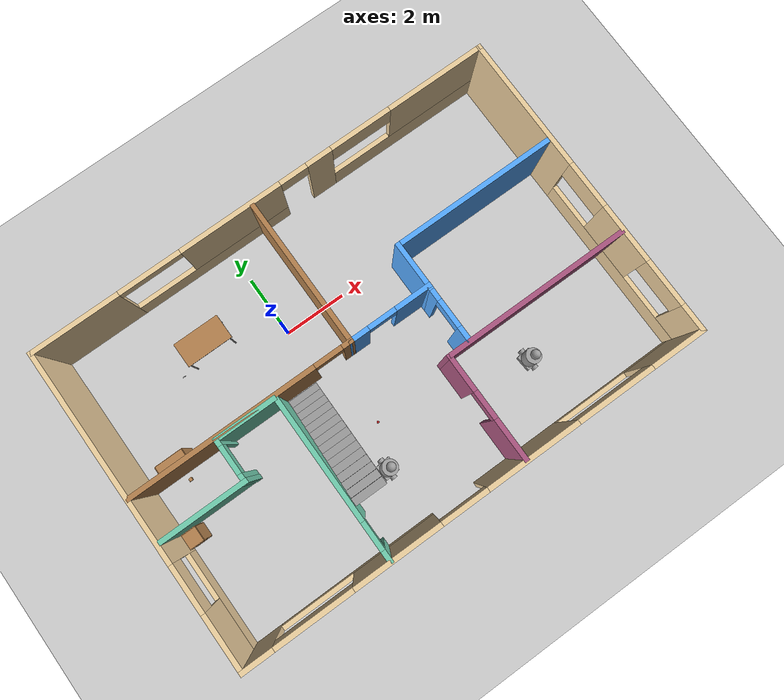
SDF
<sdf version="1.6">
 <world name="default">
  <plugin name="hello" filename="libhello.so"/>
  <light name="sun" type="directional">
   <pose>0 0 10 0 -0 0</pose>
   <diffuse>0.8 0.8 0.8 1</diffuse>
   <specular>0.2 0.2 0.2 1</specular>
   <attenuation>
    <range>1000</range>
    <constant>0.9</constant>
    <linear>0.01</linear>
    <quadratic>0.001</quadratic>
   </attenuation>
   <direction>-0.5 0.1 -0.9</direction>
  </light>
  <model name="ground_plane">
   <static>1</static>
   <link name="link">
    <collision name="collision">
     <geometry><plane><normal>0 0 1</normal><size>100 100</size></plane></geometry>
     <surface>
      <contact><collide_bitmask>65535</collide_bitmask></contact>
      <friction><ode><mu>100</mu><mu2>50</mu2></ode></friction>
     </surface>
    </collision>
    <visual name="visual">
     <cast_shadows>0</cast_shadows>
     <geometry><plane><normal>0 0 1</normal><size>100 100</size></plane></geometry>
     <material>
      <script><uri>file://media/materials/scripts/gazebo.material</uri><name>Gazebo/Grey</name></script>
     </material>
    </visual>
   </link>
  </model>
  <gravity>0 0 -9.8</gravity>
  <magnetic_field>6e-06 2.3e-05 -4.2e-05</magnetic_field>
  <atmosphere type="adiabatic"/>
  <physics name="default_physics" default="0" type="ode">
   <max_step_size>0.001</max_step_size>
   <real_time_factor>1</real_time_factor>
   <real_time_update_rate>1000</real_time_update_rate>
  </physics>
  <scene><ambient>0.4 0.4 0.4 1</ambient><background>0.7 0.7 0.7 1</background><shadows>1</shadows></scene>
  <spherical_coordinates>
   <surface_model>EARTH_WGS84</surface_model>
   <latitude_deg>0</latitude_deg>
   <longitude_deg>0</longitude_deg>
   <elevation>0</elevation>
   <heading_deg>0</heading_deg>
  </spherical_coordinates>
  <model name="MyBuilding">
   <pose>1.58731 -1.90203 0 0 -0 0</pose>
   <link name="Stairs_0">
    <visual name="Stairs_0_Visual_0">
     <pose>-2.26321 0.057041 0.083333 0 -0 0</pose>
     <geometry><box><size>1 0.233333 0.166667</size></box></geometry>
     <material>
      <script><uri>file://media/materials/scripts/gazebo.material</uri><name>Gazebo/Grey</name></script>
      <ambient>1 1 1 1</ambient>
     </material>
     <meta><layer>0</layer></meta>
    </visual>
    <collision name="Stairs_0_Collision_0">
     <geometry><box><size>1 0.233333 0.166667</size></box></geometry>
     <pose>-2.26321 0.057041 0.083333 0 -0 0</pose>
    </collision>
    <visual name="Stairs_0_Visual_1">
     <pose>-2.26321 -0.176293 0.25 0 -0 0</pose>
     <geometry><box><size>1 0.233333 0.166667</size></box></geometry>
     <material>
      <script><uri>file://media/materials/scripts/gazebo.material</uri><name>Gazebo/Grey</name></script>
      <ambient>1 1 1 1</ambient>
     </material>
     <meta><layer>0</layer></meta>
    </visual>
    <collision name="Stairs_0_Collision_1">
     <geometry><box><size>1 0.233333 0.166667</size></box></geometry>
     <pose>-2.26321 -0.176293 0.25 0 -0 0</pose>
    </collision>
    <visual name="Stairs_0_Visual_2">
     <pose>-2.26321 -0.409626 0.416667 0 -0 0</pose>
     <geometry><box><size>1 0.233333 0.166667</size></box></geometry>
     <material>
      <script><uri>file://media/materials/scripts/gazebo.material</uri><name>Gazebo/Grey</name></script>
      <ambient>1 1 1 1</ambient>
     </material>
     <meta><layer>0</layer></meta>
    </visual>
    <collision name="Stairs_0_Collision_2">
     <geometry><box><size>1 0.233333 0.166667</size></box></geometry>
     <pose>-2.26321 -0.409626 0.416667 0 -0 0</pose>
    </collision>
    <visual name="Stairs_0_Visual_3">
     <pose>-2.26321 -0.642959 0.583333 0 -0 0</pose>
     <geometry><box><size>1 0.233333 0.166667</size></box></geometry>
     <material>
      <script><uri>file://media/materials/scripts/gazebo.material</uri><name>Gazebo/Grey</name></script>
      <ambient>1 1 1 1</ambient>
     </material>
     <meta><layer>0</layer></meta>
    </visual>
    <collision name="Stairs_0_Collision_3">
     <geometry><box><size>1 0.233333 0.166667</size></box></geometry>
     <pose>-2.26321 -0.642959 0.583333 0 -0 0</pose>
    </collision>
    <visual name="Stairs_0_Visual_4">
     <pose>-2.26321 -0.876293 0.75 0 -0 0</pose>
     <geometry><box><size>1 0.233333 0.166667</size></box></geometry>
     <material>
      <script><uri>file://media/materials/scripts/gazebo.material</uri><name>Gazebo/Grey</name></script>
      <ambient>1 1 1 1</ambient>
     </material>
     <meta><layer>0</layer></meta>
    </visual>
    <collision name="Stairs_0_Collision_4">
     <geometry><box><size>1 0.233333 0.166667</size></box></geometry>
     <pose>-2.26321 -0.876293 0.75 0 -0 0</pose>
    </collision>
    <visual name="Stairs_0_Visual_5">
     <pose>-2.26321 -1.10963 0.916667 0 -0 0</pose>
     <geometry><box><size>1 0.233333 0.166667</size></box></geometry>
     <material>
      <script><uri>file://media/materials/scripts/gazebo.material</uri><name>Gazebo/Grey</name></script>
      <ambient>1 1 1 1</ambient>
     </material>
     <meta><layer>0</layer></meta>
    </visual>
    <collision name="Stairs_0_Collision_5">
     <geometry><box><size>1 0.233333 0.166667</size></box></geometry>
     <pose>-2.26321 -1.10963 0.916667 0 -0 0</pose>
    </collision>
    <visual name="Stairs_0_Visual_6">
     <pose>-2.26321 -1.34296 1.08333 0 -0 0</pose>
     <geometry><box><size>1 0.233333 0.166667</size></box></geometry>
     <material>
      <script><uri>file://media/materials/scripts/gazebo.material</uri><name>Gazebo/Grey</name></script>
      <ambient>1 1 1 1</ambient>
     </material>
     <meta><layer>0</layer></meta>
    </visual>
    <collision name="Stairs_0_Collision_6">
     <geometry><box><size>1 0.233333 0.166667</size></box></geometry>
     <pose>-2.26321 -1.34296 1.08333 0 -0 0</pose>
    </collision>
    <visual name="Stairs_0_Visual_7">
     <pose>-2.26321 -1.57629 1.25 0 -0 0</pose>
     <geometry><box><size>1 0.233333 0.166667</size></box></geometry>
     <material>
      <script><uri>file://media/materials/scripts/gazebo.material</uri><name>Gazebo/Grey</name></script>
      <ambient>1 1 1 1</ambient>
     </material>
     <meta><layer>0</layer></meta>
    </visual>
    <collision name="Stairs_0_Collision_7">
     <geometry><box><size>1 0.233333 0.166667</size></box></geometry>
     <pose>-2.26321 -1.57629 1.25 0 -0 0</pose>
    </collision>
    <visual name="Stairs_0_Visual_8">
     <pose>-2.26321 -1.80963 1.41667 0 -0 0</pose>
     <geometry><box><size>1 0.233333 0.166667</size></box></geometry>
     <material>
      <script><uri>file://media/materials/scripts/gazebo.material</uri><name>Gazebo/Grey</name></script>
      <ambient>1 1 1 1</ambient>
     </material>
     <meta><layer>0</layer></meta>
    </visual>
    <collision name="Stairs_0_Collision_8">
     <geometry><box><size>1 0.233333 0.166667</size></box></geometry>
     <pose>-2.26321 -1.80963 1.41667 0 -0 0</pose>
    </collision>
    <visual name="Stairs_0_Visual_9">
     <pose>-2.26321 -2.04296 1.58333 0 -0 0</pose>
     <geometry><box><size>1 0.233333 0.166667</size></box></geometry>
     <material>
      <script><uri>file://media/materials/scripts/gazebo.material</uri><name>Gazebo/Grey</name></script>
      <ambient>1 1 1 1</ambient>
     </material>
     <meta><layer>0</layer></meta>
    </visual>
    <collision name="Stairs_0_Collision_9">
     <geometry><box><size>1 0.233333 0.166667</size></box></geometry>
     <pose>-2.26321 -2.04296 1.58333 0 -0 0</pose>
    </collision>
    <visual name="Stairs_0_Visual_10">
     <pose>-2.26321 -2.27629 1.75 0 -0 0</pose>
     <geometry><box><size>1 0.233333 0.166667</size></box></geometry>
     <material>
      <script><uri>file://media/materials/scripts/gazebo.material</uri><name>Gazebo/Grey</name></script>
      <ambient>1 1 1 1</ambient>
     </material>
     <meta><layer>0</layer></meta>
    </visual>
    <collision name="Stairs_0_Collision_10">
     <geometry><box><size>1 0.233333 0.166667</size></box></geometry>
     <pose>-2.26321 -2.27629 1.75 0 -0 0</pose>
    </collision>
    <visual name="Stairs_0_Visual_11">
     <pose>-2.26321 -2.50963 1.91667 0 -0 0</pose>
     <geometry><box><size>1 0.233333 0.166667</size></box></geometry>
     <material>
      <script><uri>file://media/materials/scripts/gazebo.material</uri><name>Gazebo/Grey</name></script>
      <ambient>1 1 1 1</ambient>
     </material>
     <meta><layer>0</layer></meta>
    </visual>
    <collision name="Stairs_0_Collision_11">
     <geometry><box><size>1 0.233333 0.166667</size></box></geometry>
     <pose>-2.26321 -2.50963 1.91667 0 -0 0</pose>
    </collision>
    <visual name="Stairs_0_Visual_12">
     <pose>-2.26321 -2.74296 2.08333 0 -0 0</pose>
     <geometry><box><size>1 0.233333 0.166667</size></box></geometry>
     <material>
      <script><uri>file://media/materials/scripts/gazebo.material</uri><name>Gazebo/Grey</name></script>
      <ambient>1 1 1 1</ambient>
     </material>
     <meta><layer>0</layer></meta>
    </visual>
    <collision name="Stairs_0_Collision_12">
     <geometry><box><size>1 0.233333 0.166667</size></box></geometry>
     <pose>-2.26321 -2.74296 2.08333 0 -0 0</pose>
    </collision>
    <visual name="Stairs_0_Visual_13">
     <pose>-2.26321 -2.97629 2.25 0 -0 0</pose>
     <geometry><box><size>1 0.233333 0.166667</size></box></geometry>
     <material>
      <script><uri>file://media/materials/scripts/gazebo.material</uri><name>Gazebo/Grey</name></script>
      <ambient>1 1 1 1</ambient>
     </material>
     <meta><layer>0</layer></meta>
    </visual>
    <collision name="Stairs_0_Collision_13">
     <geometry><box><size>1 0.233333 0.166667</size></box></geometry>
     <pose>-2.26321 -2.97629 2.25 0 -0 0</pose>
    </collision>
    <visual name="Stairs_0_Visual_14">
     <pose>-2.26321 -3.20963 2.41667 0 -0 0</pose>
     <geometry><box><size>1 0.233333 0.166667</size></box></geometry>
     <material>
      <script><uri>file://media/materials/scripts/gazebo.material</uri><name>Gazebo/Grey</name></script>
      <ambient>1 1 1 1</ambient>
     </material>
     <meta><layer>0</layer></meta>
    </visual>
    <collision name="Stairs_0_Collision_14">
     <geometry><box><size>1 0.233333 0.166667</size></box></geometry>
     <pose>-2.26321 -3.20963 2.41667 0 -0 0</pose>
    </collision>
   </link>
   <link name="Wall_24">
    <pose>-7.5 0 0 0 0 -1.5708</pose>
    <visual name="Wall_24_Visual_0">
     <pose>-1.66537 0 1.25 0 -0 0</pose>
     <geometry><box><size>6.81926 0.15 2.5</size></box></geometry>
     <material>
      <script><uri>file://media/materials/scripts/gazebo.material</uri><name>Gazebo/Grey</name></script>
      <ambient>0.921569 0.807843 0.615686 1</ambient>
     </material>
     <meta><layer>0</layer></meta>
    </visual>
    <collision name="Wall_24_Collision_0">
     <geometry><box><size>6.81926 0.15 2.5</size></box></geometry>
     <pose>-1.66537 0 1.25 0 -0 0</pose>
    </collision>
    <visual name="Wall_24_Visual_1">
     <pose>3.40963 0 0.35 0 -0 0</pose>
     <geometry><box><size>3.33074 0.15 0.7</size></box></geometry>
     <material>
      <script><uri>file://media/materials/scripts/gazebo.material</uri><name>Gazebo/Grey</name></script>
      <ambient>0.921569 0.807843 0.615686 1</ambient>
     </material>
     <meta><layer>0</layer></meta>
    </visual>
    <collision name="Wall_24_Collision_1">
     <geometry><box><size>3.33074 0.15 0.7</size></box></geometry>
     <pose>3.40963 0 0.35 0 -0 0</pose>
    </collision>
    <visual name="Wall_24_Visual_2">
     <pose>4.15963 0 1.6 0 -0 0</pose>
     <geometry><box><size>1.83074 0.15 1.8</size></box></geometry>
     <material>
      <script><uri>file://media/materials/scripts/gazebo.material</uri><name>Gazebo/Grey</name></script>
      <ambient>0.921569 0.807843 0.615686 1</ambient>
     </material>
     <meta><layer>0</layer></meta>
    </visual>
    <collision name="Wall_24_Collision_2">
     <geometry><box><size>1.83074 0.15 1.8</size></box></geometry>
     <pose>4.15963 0 1.6 0 -0 0</pose>
    </collision>
    <visual name="Wall_24_Visual_3">
     <pose>2.49426 0 2.1 0 -0 0</pose>
     <geometry><box><size>1.5 0.15 0.8</size></box></geometry>
     <material>
      <script><uri>file://media/materials/scripts/gazebo.material</uri><name>Gazebo/Grey</name></script>
      <ambient>0.921569 0.807843 0.615686 1</ambient>
     </material>
     <meta><layer>0</layer></meta>
    </visual>
    <collision name="Wall_24_Collision_3">
     <geometry><box><size>1.5 0.15 0.8</size></box></geometry>
     <pose>2.49426 0 2.1 0 -0 0</pose>
    </collision>
   </link>
   <link name="Wall_25">
    <pose>0 -5 0 0 -0 0</pose>
    <visual name="Wall_25_Visual_0">
     <pose>-7.05279 0 1.25 0 -0 0</pose>
     <geometry><box><size>1.04517 0.15 2.5</size></box></geometry>
     <material>
      <script><uri>file://media/materials/scripts/gazebo.material</uri><name>Gazebo/Grey</name></script>
      <ambient>0.921569 0.807843 0.615686 1</ambient>
     </material>
     <meta><layer>0</layer></meta>
    </visual>
    <collision name="Wall_25_Collision_0">
     <geometry><box><size>1.04517 0.15 2.5</size></box></geometry>
     <pose>-7.05279 0 1.25 0 -0 0</pose>
    </collision>
    <visual name="Wall_25_Visual_1">
     <pose>1.78979 0 1.25 0 -0 0</pose>
     <geometry><box><size>3 0.15 2.5</size></box></geometry>
     <material>
      <script><uri>file://media/materials/scripts/gazebo.material</uri><name>Gazebo/Grey</name></script>
      <ambient>0.921569 0.807843 0.615686 1</ambient>
     </material>
     <meta><layer>0</layer></meta>
    </visual>
    <collision name="Wall_25_Collision_1">
     <geometry><box><size>3 0.15 2.5</size></box></geometry>
     <pose>1.78979 0 1.25 0 -0 0</pose>
    </collision>
    <visual name="Wall_25_Visual_2">
     <pose>-3.87021 0 0.175 0 -0 0</pose>
     <geometry><box><size>5.32 0.15 0.35</size></box></geometry>
     <material>
      <script><uri>file://media/materials/scripts/gazebo.material</uri><name>Gazebo/Grey</name></script>
      <ambient>0.921569 0.807843 0.615686 1</ambient>
     </material>
     <meta><layer>0</layer></meta>
    </visual>
    <collision name="Wall_25_Collision_2">
     <geometry><box><size>5.32 0.15 0.35</size></box></geometry>
     <pose>-3.87021 0 0.175 0 -0 0</pose>
    </collision>
    <visual name="Wall_25_Visual_3">
     <pose>5.43258 0 0.175 0 -0 0</pose>
     <geometry><box><size>4.28558 0.15 0.35</size></box></geometry>
     <material>
      <script><uri>file://media/materials/scripts/gazebo.material</uri><name>Gazebo/Grey</name></script>
      <ambient>0.921569 0.807843 0.615686 1</ambient>
     </material>
     <meta><layer>0</layer></meta>
    </visual>
    <collision name="Wall_25_Collision_3">
     <geometry><box><size>4.28558 0.15 0.35</size></box></geometry>
     <pose>5.43258 0 0.175 0 -0 0</pose>
    </collision>
    <visual name="Wall_25_Visual_4">
     <pose>-2.62021 0 1.425 0 -0 0</pose>
     <geometry><box><size>2.82 0.15 2.15</size></box></geometry>
     <material>
      <script><uri>file://media/materials/scripts/gazebo.material</uri><name>Gazebo/Grey</name></script>
      <ambient>0.921569 0.807843 0.615686 1</ambient>
     </material>
     <meta><layer>0</layer></meta>
    </visual>
    <collision name="Wall_25_Collision_4">
     <geometry><box><size>2.82 0.15 2.15</size></box></geometry>
     <pose>-2.62021 0 1.425 0 -0 0</pose>
    </collision>
    <visual name="Wall_25_Visual_5">
     <pose>-2.62021 0 1.425 0 -0 0</pose>
     <geometry><box><size>2.82 0.15 2.15</size></box></geometry>
     <material>
      <script><uri>file://media/materials/scripts/gazebo.material</uri><name>Gazebo/Grey</name></script>
      <ambient>0.921569 0.807843 0.615686 1</ambient>
     </material>
     <meta><layer>0</layer></meta>
    </visual>
    <collision name="Wall_25_Collision_5">
     <geometry><box><size>2.82 0.15 2.15</size></box></geometry>
     <pose>-2.62021 0 1.425 0 -0 0</pose>
    </collision>
    <visual name="Wall_25_Visual_6">
     <pose>6.68258 0 1.425 0 -0 0</pose>
     <geometry><box><size>1.78558 0.15 2.15</size></box></geometry>
     <material>
      <script><uri>file://media/materials/scripts/gazebo.material</uri><name>Gazebo/Grey</name></script>
      <ambient>0.921569 0.807843 0.615686 1</ambient>
     </material>
     <meta><layer>0</layer></meta>
    </visual>
    <collision name="Wall_25_Collision_6">
     <geometry><box><size>1.78558 0.15 2.15</size></box></geometry>
     <pose>6.68258 0 1.425 0 -0 0</pose>
    </collision>
    <visual name="Wall_25_Visual_7">
     <pose>-5.28021 0 2.175 0 -0 0</pose>
     <geometry><box><size>2.5 0.15 0.65</size></box></geometry>
     <material>
      <script><uri>file://media/materials/scripts/gazebo.material</uri><name>Gazebo/Grey</name></script>
      <ambient>0.921569 0.807843 0.615686 1</ambient>
     </material>
     <meta><layer>0</layer></meta>
    </visual>
    <collision name="Wall_25_Collision_7">
     <geometry><box><size>2.5 0.15 0.65</size></box></geometry>
     <pose>-5.28021 0 2.175 0 -0 0</pose>
    </collision>
    <visual name="Wall_25_Visual_8">
     <pose>4.53979 0 2.175 0 -0 0</pose>
     <geometry><box><size>2.5 0.15 0.65</size></box></geometry>
     <material>
      <script><uri>file://media/materials/scripts/gazebo.material</uri><name>Gazebo/Grey</name></script>
      <ambient>0.921569 0.807843 0.615686 1</ambient>
     </material>
     <meta><layer>0</layer></meta>
    </visual>
    <collision name="Wall_25_Collision_8">
     <geometry><box><size>2.5 0.15 0.65</size></box></geometry>
     <pose>4.53979 0 2.175 0 -0 0</pose>
    </collision>
    <visual name="Wall_25_Visual_9">
     <pose>-0.460207 0 2.25 0 -0 0</pose>
     <geometry><box><size>1.5 0.15 0.5</size></box></geometry>
     <material>
      <script><uri>file://media/materials/scripts/gazebo.material</uri><name>Gazebo/Grey</name></script>
      <ambient>0.921569 0.807843 0.615686 1</ambient>
     </material>
     <meta><layer>0</layer></meta>
    </visual>
    <collision name="Wall_25_Collision_9">
     <geometry><box><size>1.5 0.15 0.5</size></box></geometry>
     <pose>-0.460207 0 2.25 0 -0 0</pose>
    </collision>
    <visual name="Wall_25_Visual_10">
     <pose>-0.460207 0 2.25 0 -0 0</pose>
     <geometry><box><size>1.5 0.15 0.5</size></box></geometry>
     <material>
      <script><uri>file://media/materials/scripts/gazebo.material</uri><name>Gazebo/Grey</name></script>
      <ambient>0.921569 0.807843 0.615686 1</ambient>
     </material>
     <meta><layer>0</layer></meta>
    </visual>
    <collision name="Wall_25_Collision_10">
     <geometry><box><size>1.5 0.15 0.5</size></box></geometry>
     <pose>-0.460207 0 2.25 0 -0 0</pose>
    </collision>
   </link>
   <link name="Wall_28">
    <pose>-2.855 -2.417 0 0 -0 1.5708</pose>
    <visual name="Wall_28_Visual_0">
     <pose>-2.42597 0 1.25 0 -0 0</pose>
     <geometry><box><size>0.39806 0.15 2.5</size></box></geometry>
     <material>
      <script><uri>file://media/materials/scripts/gazebo.material</uri><name>Gazebo/Grey</name></script>
      <ambient>0.435294 0.796078 0.67451 1</ambient>
     </material>
     <meta><layer>0</layer></meta>
    </visual>
    <collision name="Wall_28_Collision_0">
     <geometry><box><size>0.39806 0.15 2.5</size></box></geometry>
     <pose>-2.42597 0 1.25 0 -0 0</pose>
    </collision>
    <visual name="Wall_28_Visual_1">
     <pose>0.64903 0 1.25 0 -0 0</pose>
     <geometry><box><size>3.95194 0.15 2.5</size></box></geometry>
     <material>
      <script><uri>file://media/materials/scripts/gazebo.material</uri><name>Gazebo/Grey</name></script>
      <ambient>0.435294 0.796078 0.67451 1</ambient>
     </material>
     <meta><layer>0</layer></meta>
    </visual>
    <collision name="Wall_28_Collision_1">
     <geometry><box><size>3.95194 0.15 2.5</size></box></geometry>
     <pose>0.64903 0 1.25 0 -0 0</pose>
    </collision>
    <visual name="Wall_28_Visual_2">
     <pose>-1.77694 0 2.25 0 -0 0</pose>
     <geometry><box><size>0.9 0.15 0.5</size></box></geometry>
     <material>
      <script><uri>file://media/materials/scripts/gazebo.material</uri><name>Gazebo/Grey</name></script>
      <ambient>0.435294 0.796078 0.67451 1</ambient>
     </material>
     <meta><layer>0</layer></meta>
    </visual>
    <collision name="Wall_28_Collision_2">
     <geometry><box><size>0.9 0.15 0.5</size></box></geometry>
     <pose>-1.77694 0 2.25 0 -0 0</pose>
    </collision>
   </link>
   <link name="Wall_3">
    <pose>0 5 0 0 -0 0</pose>
    <visual name="Wall_3_Visual_0">
     <pose>-6.1376 0 1.25 0 -0 0</pose>
     <geometry><box><size>2.87479 0.15 2.5</size></box></geometry>
     <material>
      <script><uri>file://media/materials/scripts/gazebo.material</uri><name>Gazebo/Grey</name></script>
      <ambient>0.921569 0.807843 0.615686 1</ambient>
     </material>
     <meta><layer>0</layer></meta>
    </visual>
    <collision name="Wall_3_Collision_0">
     <geometry><box><size>2.87479 0.15 2.5</size></box></geometry>
     <pose>-6.1376 0 1.25 0 -0 0</pose>
    </collision>
    <visual name="Wall_3_Visual_1">
     <pose>1.92479 0 1.25 0 -0 0</pose>
     <geometry><box><size>0.83 0.15 2.5</size></box></geometry>
     <material>
      <script><uri>file://media/materials/scripts/gazebo.material</uri><name>Gazebo/Grey</name></script>
      <ambient>0.921569 0.807843 0.615686 1</ambient>
     </material>
     <meta><layer>0</layer></meta>
    </visual>
    <collision name="Wall_3_Collision_1">
     <geometry><box><size>0.83 0.15 2.5</size></box></geometry>
     <pose>1.92479 0 1.25 0 -0 0</pose>
    </collision>
    <visual name="Wall_3_Visual_2">
     <pose>-2.04521 0 0.35 0 -0 0</pose>
     <geometry><box><size>5.31 0.15 0.7</size></box></geometry>
     <material>
      <script><uri>file://media/materials/scripts/gazebo.material</uri><name>Gazebo/Grey</name></script>
      <ambient>0.921569 0.807843 0.615686 1</ambient>
     </material>
     <meta><layer>0</layer></meta>
    </visual>
    <collision name="Wall_3_Collision_2">
     <geometry><box><size>5.31 0.15 0.7</size></box></geometry>
     <pose>-2.04521 0 0.35 0 -0 0</pose>
    </collision>
    <visual name="Wall_3_Visual_3">
     <pose>4.9574 0 0.4 0 -0 0</pose>
     <geometry><box><size>5.23521 0.15 0.8</size></box></geometry>
     <material>
      <script><uri>file://media/materials/scripts/gazebo.material</uri><name>Gazebo/Grey</name></script>
      <ambient>0.921569 0.807843 0.615686 1</ambient>
     </material>
     <meta><layer>0</layer></meta>
    </visual>
    <collision name="Wall_3_Collision_3">
     <geometry><box><size>5.23521 0.15 0.8</size></box></geometry>
     <pose>4.9574 0 0.4 0 -0 0</pose>
    </collision>
    <visual name="Wall_3_Visual_4">
     <pose>-1.04521 0 1.6 0 -0 0</pose>
     <geometry><box><size>3.31 0.15 1.8</size></box></geometry>
     <material>
      <script><uri>file://media/materials/scripts/gazebo.material</uri><name>Gazebo/Grey</name></script>
      <ambient>0.921569 0.807843 0.615686 1</ambient>
     </material>
     <meta><layer>0</layer></meta>
    </visual>
    <collision name="Wall_3_Collision_4">
     <geometry><box><size>3.31 0.15 1.8</size></box></geometry>
     <pose>-1.04521 0 1.6 0 -0 0</pose>
    </collision>
    <visual name="Wall_3_Visual_5">
     <pose>5.9574 0 1.65 0 -0 0</pose>
     <geometry><box><size>3.23521 0.15 1.7</size></box></geometry>
     <material>
      <script><uri>file://media/materials/scripts/gazebo.material</uri><name>Gazebo/Grey</name></script>
      <ambient>0.921569 0.807843 0.615686 1</ambient>
     </material>
     <meta><layer>0</layer></meta>
    </visual>
    <collision name="Wall_3_Collision_5">
     <geometry><box><size>3.23521 0.15 1.7</size></box></geometry>
     <pose>5.9574 0 1.65 0 -0 0</pose>
    </collision>
    <visual name="Wall_3_Visual_6">
     <pose>3.33979 0 2.15 0 -0 0</pose>
     <geometry><box><size>2 0.15 0.7</size></box></geometry>
     <material>
      <script><uri>file://media/materials/scripts/gazebo.material</uri><name>Gazebo/Grey</name></script>
      <ambient>0.921569 0.807843 0.615686 1</ambient>
     </material>
     <meta><layer>0</layer></meta>
    </visual>
    <collision name="Wall_3_Collision_6">
     <geometry><box><size>2 0.15 0.7</size></box></geometry>
     <pose>3.33979 0 2.15 0 -0 0</pose>
    </collision>
    <visual name="Wall_3_Visual_7">
     <pose>1.05979 0 2.25 0 -0 0</pose>
     <geometry><box><size>0.9 0.15 0.5</size></box></geometry>
     <material>
      <script><uri>file://media/materials/scripts/gazebo.material</uri><name>Gazebo/Grey</name></script>
      <ambient>0.921569 0.807843 0.615686 1</ambient>
     </material>
     <meta><layer>0</layer></meta>
    </visual>
    <collision name="Wall_3_Collision_7">
     <geometry><box><size>0.9 0.15 0.5</size></box></geometry>
     <pose>1.05979 0 2.25 0 -0 0</pose>
    </collision>
    <visual name="Wall_3_Visual_8">
     <pose>-3.70021 0 2.35 0 -0 0</pose>
     <geometry><box><size>2 0.15 0.3</size></box></geometry>
     <material>
      <script><uri>file://media/materials/scripts/gazebo.material</uri><name>Gazebo/Grey</name></script>
      <ambient>0.921569 0.807843 0.615686 1</ambient>
     </material>
     <meta><layer>0</layer></meta>
    </visual>
    <collision name="Wall_3_Collision_8">
     <geometry><box><size>2 0.15 0.3</size></box></geometry>
     <pose>-3.70021 0 2.35 0 -0 0</pose>
    </collision>
   </link>
   <link name="Wall_33">
    <collision name="Wall_33_Collision">
     <geometry><box><size>6 0.15 2.5</size></box></geometry>
     <pose>0 0 1.25 0 -0 0</pose>
    </collision>
    <visual name="Wall_33_Visual">
     <pose>0 0 1.25 0 -0 0</pose>
     <geometry><box><size>6 0.15 2.5</size></box></geometry>
     <material>
      <script><uri>file://media/materials/scripts/gazebo.material</uri><name>Gazebo/Grey</name></script>
      <ambient>0.666667 0.333333 0.498039 1</ambient>
     </material>
     <meta><layer>0</layer></meta>
    </visual>
    <pose>4.48282 -1.58892 0 0 -0 0</pose>
   </link>
   <link name="Wall_36">
    <pose>2.24489 -0.724368 0 0 0 -1.5708</pose>
    <visual name="Wall_36_Visual_0">
     <pose>-0.697553 0 1.25 0 -0 0</pose>
     <geometry><box><size>0.354895 0.15 2.5</size></box></geometry>
     <material>
      <script><uri>file://media/materials/scripts/gazebo.material</uri><name>Gazebo/Grey</name></script>
      <ambient>0.333333 0.666667 1 1</ambient>
     </material>
     <meta><layer>0</layer></meta>
    </visual>
    <collision name="Wall_36_Collision_0">
     <geometry><box><size>0.354895 0.15 2.5</size></box></geometry>
     <pose>-0.697553 0 1.25 0 -0 0</pose>
    </collision>
    <visual name="Wall_36_Visual_1">
     <pose>0.627447 0 1.25 0 -0 0</pose>
     <geometry><box><size>0.495105 0.15 2.5</size></box></geometry>
     <material>
      <script><uri>file://media/materials/scripts/gazebo.material</uri><name>Gazebo/Grey</name></script>
      <ambient>0.333333 0.666667 1 1</ambient>
     </material>
     <meta><layer>0</layer></meta>
    </visual>
    <collision name="Wall_36_Collision_1">
     <geometry><box><size>0.495105 0.15 2.5</size></box></geometry>
     <pose>0.627447 0 1.25 0 -0 0</pose>
    </collision>
    <visual name="Wall_36_Visual_2">
     <pose>-0.070105 0 2.25 0 -0 0</pose>
     <geometry><box><size>0.9 0.15 0.5</size></box></geometry>
     <material>
      <script><uri>file://media/materials/scripts/gazebo.material</uri><name>Gazebo/Grey</name></script>
      <ambient>0.333333 0.666667 1 1</ambient>
     </material>
     <meta><layer>0</layer></meta>
    </visual>
    <collision name="Wall_36_Collision_2">
     <geometry><box><size>0.9 0.15 0.5</size></box></geometry>
     <pose>-0.070105 0 2.25 0 -0 0</pose>
    </collision>
   </link>
   <link name="Wall_38">
    <collision name="Wall_38_Collision">
     <geometry><box><size>1.75 0.15 2.5</size></box></geometry>
     <pose>0 0 1.25 0 -0 0</pose>
    </collision>
    <visual name="Wall_38_Visual">
     <pose>0 0 1.25 0 -0 0</pose>
     <geometry><box><size>1.75 0.15 2.5</size></box></geometry>
     <material>
      <script><uri>file://media/materials/scripts/gazebo.material</uri><name>Gazebo/Grey</name></script>
      <ambient>0.333333 0.666667 1 1</ambient>
     </material>
     <meta><layer>0</layer></meta>
    </visual>
    <pose>2.24489 0.875632 0 0 -0 1.5708</pose>
   </link>
   <link name="Wall_39">
    <collision name="Wall_39_Collision">
     <geometry><box><size>5.25 0.15 2.5</size></box></geometry>
     <pose>0 0 1.25 0 -0 0</pose>
    </collision>
    <visual name="Wall_39_Visual">
     <pose>0 0 1.25 0 -0 0</pose>
     <geometry><box><size>5.25 0.15 2.5</size></box></geometry>
     <material>
      <script><uri>file://media/materials/scripts/gazebo.material</uri><name>Gazebo/Grey</name></script>
      <ambient>0.333333 0.666667 1 1</ambient>
     </material>
     <meta><layer>0</layer></meta>
    </visual>
    <pose>4.79489 1.67563 0 0 -0 0</pose>
   </link>
   <link name="Wall_43">
    <pose>1.55782 -3.26392 0 0 0 -1.5708</pose>
    <visual name="Wall_43_Visual_0">
     <pose>-1.13483 0 1.25 0 -0 0</pose>
     <geometry><box><size>1.23034 0.15 2.5</size></box></geometry>
     <material>
      <script><uri>file://media/materials/scripts/gazebo.material</uri><name>Gazebo/Grey</name></script>
      <ambient>0.666667 0.333333 0.498039 1</ambient>
     </material>
     <meta><layer>0</layer></meta>
    </visual>
    <collision name="Wall_43_Collision_0">
     <geometry><box><size>1.23034 0.15 2.5</size></box></geometry>
     <pose>-1.13483 0 1.25 0 -0 0</pose>
    </collision>
    <visual name="Wall_43_Visual_1">
     <pose>1.06517 0 1.25 0 -0 0</pose>
     <geometry><box><size>1.36966 0.15 2.5</size></box></geometry>
     <material>
      <script><uri>file://media/materials/scripts/gazebo.material</uri><name>Gazebo/Grey</name></script>
      <ambient>0.666667 0.333333 0.498039 1</ambient>
     </material>
     <meta><layer>0</layer></meta>
    </visual>
    <collision name="Wall_43_Collision_1">
     <geometry><box><size>1.36966 0.15 2.5</size></box></geometry>
     <pose>1.06517 0 1.25 0 -0 0</pose>
    </collision>
    <visual name="Wall_43_Visual_2">
     <pose>-0.069658 0 2.25 0 -0 0</pose>
     <geometry><box><size>0.9 0.15 0.5</size></box></geometry>
     <material>
      <script><uri>file://media/materials/scripts/gazebo.material</uri><name>Gazebo/Grey</name></script>
      <ambient>0.666667 0.333333 0.498039 1</ambient>
     </material>
     <meta><layer>0</layer></meta>
    </visual>
    <collision name="Wall_43_Collision_2">
     <geometry><box><size>0.9 0.15 0.5</size></box></geometry>
     <pose>-0.069658 0 2.25 0 -0 0</pose>
    </collision>
   </link>
   <link name="Wall_47">
    <collision name="Wall_47_Collision">
     <geometry><box><size>2.78025 0.15 2.5</size></box></geometry>
     <pose>0 0 1.25 0 -0 0</pose>
    </collision>
    <visual name="Wall_47_Visual">
     <pose>0 0 1.25 0 -0 0</pose>
     <geometry><box><size>2.78025 0.15 2.5</size></box></geometry>
     <material>
      <script><uri>file://media/materials/scripts/gazebo.material</uri><name>Gazebo/Grey</name></script>
      <ambient>0.435294 0.796078 0.67451 1</ambient>
     </material>
     <meta><layer>0</layer></meta>
    </visual>
    <pose>-6.0579 -1.1166 0 0 -0 0</pose>
   </link>
   <link name="Wall_48">
    <pose>-4.75795 -0.45686 0 0 -0 1.57087</pose>
    <visual name="Wall_48_Visual_0">
     <pose>-0.585551 0 1.25 0 -0 0</pose>
     <geometry><box><size>0.328897 0.15 2.5</size></box></geometry>
     <material>
      <script><uri>file://media/materials/scripts/gazebo.material</uri><name>Gazebo/Grey</name></script>
      <ambient>0.435294 0.796078 0.67451 1</ambient>
     </material>
     <meta><layer>0</layer></meta>
    </visual>
    <collision name="Wall_48_Collision_0">
     <geometry><box><size>0.328897 0.15 2.5</size></box></geometry>
     <pose>-0.585551 0 1.25 0 -0 0</pose>
    </collision>
    <visual name="Wall_48_Visual_1">
     <pose>0.614449 0 1.25 0 -0 0</pose>
     <geometry><box><size>0.271103 0.15 2.5</size></box></geometry>
     <material>
      <script><uri>file://media/materials/scripts/gazebo.material</uri><name>Gazebo/Grey</name></script>
      <ambient>0.435294 0.796078 0.67451 1</ambient>
     </material>
     <meta><layer>0</layer></meta>
    </visual>
    <collision name="Wall_48_Collision_1">
     <geometry><box><size>0.271103 0.15 2.5</size></box></geometry>
     <pose>0.614449 0 1.25 0 -0 0</pose>
    </collision>
    <visual name="Wall_48_Visual_2">
     <pose>0.028897 0 2.25 0 -0 0</pose>
     <geometry><box><size>0.9 0.15 0.5</size></box></geometry>
     <material>
      <script><uri>file://media/materials/scripts/gazebo.material</uri><name>Gazebo/Grey</name></script>
      <ambient>0.435294 0.796078 0.67451 1</ambient>
     </material>
     <meta><layer>0</layer></meta>
    </visual>
    <collision name="Wall_48_Collision_2">
     <geometry><box><size>0.9 0.15 0.5</size></box></geometry>
     <pose>0.028897 0 2.25 0 -0 0</pose>
    </collision>
   </link>
   <link name="Wall_5">
    <collision name="Wall_5_Collision">
     <geometry><box><size>0.15 0.15 2.5</size></box></geometry>
     <pose>0 0 1.25 0 -0 0</pose>
    </collision>
    <visual name="Wall_5_Visual">
     <pose>0 0 1.25 0 -0 0</pose>
     <geometry><box><size>0.15 0.15 2.5</size></box></geometry>
     <material>
      <script><uri>file://media/materials/scripts/gazebo.material</uri><name>Gazebo/Grey</name></script>
      <ambient>1 1 1 1</ambient>
     </material>
     <meta><layer>0</layer></meta>
    </visual>
    <pose>7.5 5 0 0 -0 0</pose>
   </link>
   <link name="Wall_55">
    <pose>-3.901 0.285 0 0 -0 0</pose>
    <visual name="Wall_55_Visual_0">
     <pose>-0.629891 0 1.25 0 -0 0</pose>
     <geometry><box><size>5.99022 0.15 2.5</size></box></geometry>
     <material>
      <script><uri>file://media/materials/scripts/gazebo.material</uri><name>Gazebo/Wood</name></script>
      <ambient>1 1 1 1</ambient>
     </material>
     <meta><layer>0</layer></meta>
    </visual>
    <collision name="Wall_55_Collision_0">
     <geometry><box><size>5.99022 0.15 2.5</size></box></geometry>
     <pose>-0.629891 0 1.25 0 -0 0</pose>
    </collision>
    <visual name="Wall_55_Visual_1">
     <pose>3.44511 0 1.25 0 -0 0</pose>
     <geometry><box><size>0.359783 0.15 2.5</size></box></geometry>
     <material>
      <script><uri>file://media/materials/scripts/gazebo.material</uri><name>Gazebo/Wood</name></script>
      <ambient>1 1 1 1</ambient>
     </material>
     <meta><layer>0</layer></meta>
    </visual>
    <collision name="Wall_55_Collision_1">
     <geometry><box><size>0.359783 0.15 2.5</size></box></geometry>
     <pose>3.44511 0 1.25 0 -0 0</pose>
    </collision>
    <visual name="Wall_55_Visual_2">
     <pose>2.81522 0 2.25 0 -0 0</pose>
     <geometry><box><size>0.9 0.15 0.5</size></box></geometry>
     <material>
      <script><uri>file://media/materials/scripts/gazebo.material</uri><name>Gazebo/Wood</name></script>
      <ambient>1 1 1 1</ambient>
     </material>
     <meta><layer>0</layer></meta>
    </visual>
    <collision name="Wall_55_Collision_2">
     <geometry><box><size>0.9 0.15 0.5</size></box></geometry>
     <pose>2.81522 0 2.25 0 -0 0</pose>
    </collision>
   </link>
   <link name="Wall_56">
    <collision name="Wall_56_Collision">
     <geometry><box><size>4.75 0.15 2.5</size></box></geometry>
     <pose>0 0 1.25 0 -0 0</pose>
    </collision>
    <visual name="Wall_56_Visual">
     <pose>0 0 1.25 0 -0 0</pose>
     <geometry><box><size>4.75 0.15 2.5</size></box></geometry>
     <material>
      <script><uri>file://media/materials/scripts/gazebo.material</uri><name>Gazebo/Wood</name></script>
      <ambient>1 1 1 1</ambient>
     </material>
     <meta><layer>0</layer></meta>
    </visual>
    <pose>-0.351 2.585 0 0 -0 1.5708</pose>
   </link>
   <link name="Wall_58">
    <pose>0.949092 0.285065 0 0 -0 5e-05</pose>
    <visual name="Wall_58_Visual_0">
     <pose>-1.04294 0 1.25 0 -0 0</pose>
     <geometry><box><size>0.664112 0.15 2.5</size></box></geometry>
     <material>
      <script><uri>file://media/materials/scripts/gazebo.material</uri><name>Gazebo/Grey</name></script>
      <ambient>0.333333 0.666667 1 1</ambient>
     </material>
     <meta><layer>0</layer></meta>
    </visual>
    <collision name="Wall_58_Collision_0">
     <geometry><box><size>0.664112 0.15 2.5</size></box></geometry>
     <pose>-1.04294 0 1.25 0 -0 0</pose>
    </collision>
    <visual name="Wall_58_Visual_1">
     <pose>0.782056 0 1.25 0 -0 0</pose>
     <geometry><box><size>1.18589 0.15 2.5</size></box></geometry>
     <material>
      <script><uri>file://media/materials/scripts/gazebo.material</uri><name>Gazebo/Grey</name></script>
      <ambient>0.333333 0.666667 1 1</ambient>
     </material>
     <meta><layer>0</layer></meta>
    </visual>
    <collision name="Wall_58_Collision_1">
     <geometry><box><size>1.18589 0.15 2.5</size></box></geometry>
     <pose>0.782056 0 1.25 0 -0 0</pose>
    </collision>
    <visual name="Wall_58_Visual_2">
     <pose>-0.260888 0 2.25 0 -0 0</pose>
     <geometry><box><size>0.9 0.15 0.5</size></box></geometry>
     <material>
      <script><uri>file://media/materials/scripts/gazebo.material</uri><name>Gazebo/Grey</name></script>
      <ambient>0.333333 0.666667 1 1</ambient>
     </material>
     <meta><layer>0</layer></meta>
    </visual>
    <collision name="Wall_58_Collision_2">
     <geometry><box><size>0.9 0.15 0.5</size></box></geometry>
     <pose>-0.260888 0 2.25 0 -0 0</pose>
    </collision>
   </link>
   <link name="Wall_6">
    <pose>7.5 0 0 0 0 -1.5708</pose>
    <visual name="Wall_6_Visual_0">
     <pose>-2.91696 0 1.25 0 -0 0</pose>
     <geometry><box><size>4.31609 0.15 2.5</size></box></geometry>
     <material>
      <script><uri>file://media/materials/scripts/gazebo.material</uri><name>Gazebo/Grey</name></script>
      <ambient>0.921569 0.807843 0.615686 1</ambient>
     </material>
     <meta><layer>0</layer></meta>
    </visual>
    <collision name="Wall_6_Collision_0">
     <geometry><box><size>4.31609 0.15 2.5</size></box></geometry>
     <pose>-2.91696 0 1.25 0 -0 0</pose>
    </collision>
    <visual name="Wall_6_Visual_1">
     <pose>2.15804 0 0.35 0 -0 0</pose>
     <geometry><box><size>5.83392 0.15 0.7</size></box></geometry>
     <material>
      <script><uri>file://media/materials/scripts/gazebo.material</uri><name>Gazebo/Grey</name></script>
      <ambient>0.921569 0.807843 0.615686 1</ambient>
     </material>
     <meta><layer>0</layer></meta>
    </visual>
    <collision name="Wall_6_Collision_1">
     <geometry><box><size>5.83392 0.15 0.7</size></box></geometry>
     <pose>2.15804 0 0.35 0 -0 0</pose>
    </collision>
    <visual name="Wall_6_Visual_2">
     <pose>1.69267 0 1.6 0 -0 0</pose>
     <geometry><box><size>1.90318 0.15 1.8</size></box></geometry>
     <material>
      <script><uri>file://media/materials/scripts/gazebo.material</uri><name>Gazebo/Grey</name></script>
      <ambient>0.921569 0.807843 0.615686 1</ambient>
     </material>
     <meta><layer>0</layer></meta>
    </visual>
    <collision name="Wall_6_Collision_2">
     <geometry><box><size>1.90318 0.15 1.8</size></box></geometry>
     <pose>1.69267 0 1.6 0 -0 0</pose>
    </collision>
    <visual name="Wall_6_Visual_3">
     <pose>4.60963 0 1.6 0 -0 0</pose>
     <geometry><box><size>0.930737 0.15 1.8</size></box></geometry>
     <material>
      <script><uri>file://media/materials/scripts/gazebo.material</uri><name>Gazebo/Grey</name></script>
      <ambient>0.921569 0.807843 0.615686 1</ambient>
     </material>
     <meta><layer>0</layer></meta>
    </visual>
    <collision name="Wall_6_Collision_3">
     <geometry><box><size>0.930737 0.15 1.8</size></box></geometry>
     <pose>4.60963 0 1.6 0 -0 0</pose>
    </collision>
    <visual name="Wall_6_Visual_4">
     <pose>-0.008915 0 2.1 0 -0 0</pose>
     <geometry><box><size>1.5 0.15 0.8</size></box></geometry>
     <material>
      <script><uri>file://media/materials/scripts/gazebo.material</uri><name>Gazebo/Grey</name></script>
      <ambient>0.921569 0.807843 0.615686 1</ambient>
     </material>
     <meta><layer>0</layer></meta>
    </visual>
    <collision name="Wall_6_Collision_4">
     <geometry><box><size>1.5 0.15 0.8</size></box></geometry>
     <pose>-0.008915 0 2.1 0 -0 0</pose>
    </collision>
    <visual name="Wall_6_Visual_5">
     <pose>3.39426 0 2.1 0 -0 0</pose>
     <geometry><box><size>1.5 0.15 0.8</size></box></geometry>
     <material>
      <script><uri>file://media/materials/scripts/gazebo.material</uri><name>Gazebo/Grey</name></script>
      <ambient>0.921569 0.807843 0.615686 1</ambient>
     </material>
     <meta><layer>0</layer></meta>
    </visual>
    <collision name="Wall_6_Collision_5">
     <geometry><box><size>1.5 0.15 0.8</size></box></geometry>
     <pose>3.39426 0 2.1 0 -0 0</pose>
    </collision>
   </link>
   <link name="Wall_60">
    <collision name="Wall_60_Collision">
     <geometry><box><size>2 0.15 2.5</size></box></geometry>
     <pose>0 0 1.25 0 -0 0</pose>
    </collision>
    <visual name="Wall_60_Visual">
     <pose>0 0 1.25 0 -0 0</pose>
     <geometry><box><size>2 0.15 2.5</size></box></geometry>
     <material>
      <script><uri>file://media/materials/scripts/gazebo.material</uri><name>Gazebo/Grey</name></script>
      <ambient>0.435294 0.796078 0.67451 1</ambient>
     </material>
     <meta><layer>0</layer></meta>
    </visual>
    <pose>-3.833 0.218 0 0 -0 0</pose>
   </link>
   <static>1</static>
  </model>
  <model name="bookshelf">
   <static>1</static>
   <link name="link">
    <inertial><mass>1</mass></inertial>
    <collision name="back">
     <pose>0 0.005 0.6 0 -0 0</pose>
     <geometry><box><size>0.9 0.01 1.2</size></box></geometry>
    </collision>
    <visual name="visual1">
     <pose>0 0.005 0.6 0 -0 0</pose>
     <geometry><box><size>0.9 0.01 1.2</size></box></geometry>
     <material>
      <script><uri>file://media/materials/scripts/gazebo.material</uri><name>Gazebo/Wood</name></script>
     </material>
    </visual>
    <collision name="left_side">
     <pose>0.45 -0.195 0.6 0 -0 0</pose>
     <geometry><box><size>0.02 0.4 1.2</size></box></geometry>
    </collision>
    <visual name="visual2">
     <pose>0.45 -0.195 0.6 0 -0 0</pose>
     <geometry><box><size>0.02 0.4 1.2</size></box></geometry>
     <material>
      <script><uri>file://media/materials/scripts/gazebo.material</uri><name>Gazebo/Wood</name></script>
     </material>
    </visual>
    <collision name="right_side">
     <pose>-0.45 -0.195 0.6 0 -0 0</pose>
     <geometry><box><size>0.02 0.4 1.2</size></box></geometry>
    </collision>
    <visual name="visual3">
     <pose>-0.45 -0.195 0.6 0 -0 0</pose>
     <geometry><box><size>0.02 0.4 1.2</size></box></geometry>
     <material>
      <script><uri>file://media/materials/scripts/gazebo.material</uri><name>Gazebo/Wood</name></script>
     </material>
    </visual>
    <collision name="bottom">
     <pose>0 -0.195 0.03 0 -0 0</pose>
     <geometry><box><size>0.88 0.4 0.06</size></box></geometry>
    </collision>
    <visual name="visual4">
     <pose>0 -0.195 0.03 0 -0 0</pose>
     <geometry><box><size>0.88 0.4 0.06</size></box></geometry>
     <material>
      <script><uri>file://media/materials/scripts/gazebo.material</uri><name>Gazebo/Wood</name></script>
     </material>
    </visual>
    <collision name="top">
     <pose>0 -0.195 1.19 0 -0 0</pose>
     <geometry><box><size>0.88 0.4 0.02</size></box></geometry>
    </collision>
    <visual name="visual5">
     <pose>0 -0.195 1.19 0 -0 0</pose>
     <geometry><box><size>0.88 0.4 0.02</size></box></geometry>
     <material>
      <script><uri>file://media/materials/scripts/gazebo.material</uri><name>Gazebo/Wood</name></script>
     </material>
    </visual>
    <collision name="low_shelf">
     <pose>0 -0.195 0.43 0 -0 0</pose>
     <geometry><box><size>0.88 0.4 0.02</size></box></geometry>
    </collision>
    <visual name="visual6">
     <pose>0 -0.195 0.43 0 -0 0</pose>
     <geometry><box><size>0.88 0.4 0.02</size></box></geometry>
     <material>
      <script><uri>file://media/materials/scripts/gazebo.material</uri><name>Gazebo/Wood</name></script>
     </material>
    </visual>
    <collision name="high_shelf">
     <pose>0 -0.195 0.8 0 -0 0</pose>
     <geometry><box><size>0.88 0.4 0.02</size></box></geometry>
    </collision>
    <visual name="visual7">
     <pose>0 -0.195 0.8 0 -0 0</pose>
     <geometry><box><size>0.88 0.4 0.02</size></box></geometry>
     <material>
      <script><uri>file://media/materials/scripts/gazebo.material</uri><name>Gazebo/Wood</name></script>
     </material>
    </visual>
   </link>
   <pose>-4.75283 -1.15714 0 0 -0 0</pose>
  </model>
  <model name="cabinet">
   <static>1</static>
   <link name="cabinet_bottom_plate">
    <inertial>
     <pose>0 0 -1 0 -0 0</pose>
     <inertia><ixx>2.05</ixx><ixy>0</ixy><ixz>0</ixz><iyy>2.05</iyy><iyz>0</iyz><izz>2.05</izz></inertia>
     <mass>25</mass>
    </inertial>
    <collision name="cabinet_bottom_plate_geom">
     <pose>0 0 0.01 0 -0 0</pose>
     <geometry><box><size>0.45 0.45 0.02</size></box></geometry>
    </collision>
    <visual name="cabinet_bottom_plate_geom_visual">
     <pose>0 0 0.01 0 -0 0</pose>
     <geometry><box><size>0.45 0.45 0.02</size></box></geometry>
     <material>
      <script><uri>file://media/materials/scripts/gazebo.material</uri><name>Gazebo/Wood</name></script>
     </material>
    </visual>
    <collision name="cabinet_bottom_plate_geom_cabinet_back_plate">
     <pose>0.235 0 0.51 0 -0 0</pose>
     <geometry><box><size>0.02 0.45 1.02</size></box></geometry>
    </collision>
    <visual name="cabinet_bottom_plate_geom_cabinet_back_plate_visual">
     <pose>0.235 0 0.51 0 -0 0</pose>
     <geometry><box><size>0.02 0.45 1.02</size></box></geometry>
     <material>
      <script><uri>file://media/materials/scripts/gazebo.material</uri><name>Gazebo/Wood</name></script>
     </material>
    </visual>
    <collision name="cabinet_bottom_plate_geom_cabinet_left_plate">
     <pose>0 0.235 0.51 0 -0 0</pose>
     <geometry><box><size>0.45 0.02 1.02</size></box></geometry>
    </collision>
    <visual name="cabinet_bottom_plate_geom_cabinet_left_plate_visual">
     <pose>0 0.235 0.51 0 -0 0</pose>
     <geometry><box><size>0.45 0.02 1.02</size></box></geometry>
     <material>
      <script><uri>file://media/materials/scripts/gazebo.material</uri><name>Gazebo/Wood</name></script>
     </material>
    </visual>
    <collision name="cabinet_bottom_plate_geom_cabinet_middle_plate">
     <pose>0 0 0.51 0 -0 0</pose>
     <geometry><box><size>0.45 0.45 0.02</size></box></geometry>
    </collision>
    <visual name="cabinet_bottom_plate_geom_cabinet_middle_plate_visual">
     <pose>0 0 0.51 0 -0 0</pose>
     <geometry><box><size>0.45 0.45 0.02</size></box></geometry>
     <material>
      <script><uri>file://media/materials/scripts/gazebo.material</uri><name>Gazebo/Wood</name></script>
     </material>
    </visual>
    <collision name="cabinet_bottom_plate_geom_cabinet_right_plate">
     <pose>0 -0.235 0.51 0 -0 0</pose>
     <geometry><box><size>0.45 0.02 1.02</size></box></geometry>
    </collision>
    <visual name="cabinet_bottom_plate_geom_cabinet_right_plate_visual">
     <pose>0 -0.235 0.51 0 -0 0</pose>
     <geometry><box><size>0.45 0.02 1.02</size></box></geometry>
     <material>
      <script><uri>file://media/materials/scripts/gazebo.material</uri><name>Gazebo/Wood</name></script>
     </material>
    </visual>
    <collision name="cabinet_bottom_plate_geom_cabinet_top_plate">
     <pose>0 0 1.01 0 -0 0</pose>
     <geometry><box><size>0.45 0.45 0.02</size></box></geometry>
    </collision>
    <visual name="cabinet_bottom_plate_geom_cabinet_top_plate_visual">
     <pose>0 0 1.01 0 -0 0</pose>
     <geometry><box><size>0.45 0.45 0.02</size></box></geometry>
     <material>
      <script><uri>file://media/materials/scripts/gazebo.material</uri><name>Gazebo/Wood</name></script>
     </material>
    </visual>
   </link>
   <pose>-5.45597 -3.36278 0 0 -0 0</pose>
  </model>
  <model name="RoboModel">
   <link name="link_0">
    <pose>0.004 1e-06 -0.17 0 -0 0</pose>
    <inertial>
     <mass>1</mass>
     <inertia>
      <ixx>0.166667</ixx>
      <ixy>0</ixy>
      <ixz>0</ixz>
      <iyy>0.166667</iyy>
      <iyz>0</iyz>
      <izz>0.166667</izz>
     </inertia>
    </inertial>
    <visual name="visual">
     <geometry><box><size>0.5 0.5 0.1</size></box></geometry>
     <material>
      <lighting>1</lighting>
      <script><uri>file://media/materials/scripts/gazebo.material</uri><name>Gazebo/Grey</name></script>
      <shader type="pixel"><normal_map>__default__</normal_map></shader>
      <ambient>0.3 0.3 0.3 1</ambient>
      <diffuse>0.7 0.7 0.7 1</diffuse>
      <specular>0.01 0.01 0.01 1</specular>
      <emissive>0 0 0 1</emissive>
     </material>
    </visual>
    <collision name="collision">
     <geometry><box><size>0.5 0.5 0.1</size></box></geometry>
     <surface>
      <friction>
       <ode><mu>1</mu><mu2>1</mu2><fdir1>0 0 0</fdir1><slip1>0</slip1><slip2>0</slip2></ode>
       <torsional>
        <coefficient>1</coefficient>
        <patch_radius>0</patch_radius>
        <surface_radius>0</surface_radius>
        <use_patch_radius>1</use_patch_radius>
        <ode><slip>0</slip></ode>
       </torsional>
      </friction>
      <bounce><restitution_coefficient>0</restitution_coefficient><threshold>1e+06</threshold></bounce>
      <contact>
       <collide_without_contact>0</collide_without_contact>
       <collide_without_contact_bitmask>1</collide_without_contact_bitmask>
       <collide_bitmask>1</collide_bitmask>
       <ode>
        <soft_cfm>0</soft_cfm>
        <soft_erp>0.2</soft_erp>
        <kp>1e+13</kp>
        <kd>1</kd>
        <max_vel>0.01</max_vel>
        <min_depth>0</min_depth>
       </ode>
       <bullet>
        <split_impulse>1</split_impulse>
        <split_impulse_penetration_threshold>-0.01</split_impulse_penetration_threshold>
        <soft_cfm>0</soft_cfm>
        <soft_erp>0.2</soft_erp>
        <kp>1e+13</kp>
        <kd>1</kd>
       </bullet>
      </contact>
     </surface>
    </collision>
   </link>
   <link name="link_1">
    <pose>0.004 1e-06 0.08 0 -0 0</pose>
    <inertial>
     <mass>1</mass>
     <inertia><ixx>0.145833</ixx><ixy>0</ixy><ixz>0</ixz><iyy>0.145833</iyy><iyz>0</iyz><izz>0.125</izz></inertia>
    </inertial>
    <visual name="visual">
     <geometry><cylinder><radius>0.25</radius><length>0.4</length></cylinder></geometry>
     <material>
      <lighting>1</lighting>
      <script><uri>file://media/materials/scripts/gazebo.material</uri><name>Gazebo/Grey</name></script>
      <shader type="pixel"><normal_map>__default__</normal_map></shader>
      <ambient>0.3 0.3 0.3 1</ambient>
      <diffuse>0.7 0.7 0.7 1</diffuse>
      <specular>0.01 0.01 0.01 1</specular>
      <emissive>0 0 0 1</emissive>
     </material>
    </visual>
    <collision name="collision">
     <geometry><cylinder><radius>0.25</radius><length>0.4</length></cylinder></geometry>
     <surface>
      <friction>
       <ode><mu>1</mu><mu2>1</mu2><fdir1>0 0 0</fdir1><slip1>0</slip1><slip2>0</slip2></ode>
       <torsional>
        <coefficient>1</coefficient>
        <patch_radius>0</patch_radius>
        <surface_radius>0</surface_radius>
        <use_patch_radius>1</use_patch_radius>
        <ode><slip>0</slip></ode>
       </torsional>
      </friction>
      <bounce><restitution_coefficient>0</restitution_coefficient><threshold>1e+06</threshold></bounce>
      <contact>
       <collide_without_contact>0</collide_without_contact>
       <collide_without_contact_bitmask>1</collide_without_contact_bitmask>
       <collide_bitmask>1</collide_bitmask>
       <ode>
        <soft_cfm>0</soft_cfm>
        <soft_erp>0.2</soft_erp>
        <kp>1e+13</kp>
        <kd>1</kd>
        <max_vel>0.01</max_vel>
        <min_depth>0</min_depth>
       </ode>
       <bullet>
        <split_impulse>1</split_impulse>
        <split_impulse_penetration_threshold>-0.01</split_impulse_penetration_threshold>
        <soft_cfm>0</soft_cfm>
        <soft_erp>0.2</soft_erp>
        <kp>1e+13</kp>
        <kd>1</kd>
       </bullet>
      </contact>
     </surface>
    </collision>
   </link>
   <link name="link_4">
    <pose>0.004 1e-06 0.43 0 -0 0</pose>
    <inertial>
     <mass>1</mass>
     <inertia><ixx>0.1</ixx><ixy>0</ixy><ixz>0</ixz><iyy>0.1</iyy><iyz>0</iyz><izz>0.1</izz></inertia>
    </inertial>
    <visual name="visual">
     <geometry><sphere><radius>0.15</radius></sphere></geometry>
     <material>
      <lighting>1</lighting>
      <script><uri>file://media/materials/scripts/gazebo.material</uri><name>Gazebo/Grey</name></script>
      <shader type="pixel"><normal_map>__default__</normal_map></shader>
      <ambient>0.3 0.3 0.3 1</ambient>
      <diffuse>0.7 0.7 0.7 1</diffuse>
      <specular>0.01 0.01 0.01 1</specular>
      <emissive>0 0 0 1</emissive>
     </material>
    </visual>
    <collision name="collision">
     <geometry><sphere><radius>0.15</radius></sphere></geometry>
     <surface>
      <friction>
       <ode><mu>1</mu><mu2>1</mu2><fdir1>0 0 0</fdir1><slip1>0</slip1><slip2>0</slip2></ode>
       <torsional>
        <coefficient>1</coefficient>
        <patch_radius>0</patch_radius>
        <surface_radius>0</surface_radius>
        <use_patch_radius>1</use_patch_radius>
        <ode><slip>0</slip></ode>
       </torsional>
      </friction>
      <bounce><restitution_coefficient>0</restitution_coefficient><threshold>1e+06</threshold></bounce>
      <contact>
       <collide_without_contact>0</collide_without_contact>
       <collide_without_contact_bitmask>1</collide_without_contact_bitmask>
       <collide_bitmask>1</collide_bitmask>
       <ode>
        <soft_cfm>0</soft_cfm>
        <soft_erp>0.2</soft_erp>
        <kp>1e+13</kp>
        <kd>1</kd>
        <max_vel>0.01</max_vel>
        <min_depth>0</min_depth>
       </ode>
       <bullet>
        <split_impulse>1</split_impulse>
        <split_impulse_penetration_threshold>-0.01</split_impulse_penetration_threshold>
        <soft_cfm>0</soft_cfm>
        <soft_erp>0.2</soft_erp>
        <kp>1e+13</kp>
        <kd>1</kd>
       </bullet>
      </contact>
     </surface>
    </collision>
   </link>
   <link name="link_5">
    <pose>-0.016 -0.300012 -0.17 1.5707 -0 0</pose>
    <inertial>
     <mass>1</mass>
     <inertia><ixx>0.145833</ixx><ixy>0</ixy><ixz>0</ixz><iyy>0.145833</iyy><iyz>0</iyz><izz>0.125</izz></inertia>
    </inertial>
    <visual name="visual">
     <geometry><cylinder><radius>0.1</radius><length>0.1</length></cylinder></geometry>
     <material>
      <lighting>1</lighting>
      <script><uri>file://media/materials/scripts/gazebo.material</uri><name>Gazebo/Grey</name></script>
      <shader type="pixel"><normal_map>__default__</normal_map></shader>
      <ambient>0.3 0.3 0.3 1</ambient>
      <diffuse>0.7 0.7 0.7 1</diffuse>
      <specular>0.01 0.01 0.01 1</specular>
      <emissive>0 0 0 1</emissive>
     </material>
    </visual>
    <collision name="collision">
     <geometry><cylinder><radius>0.1</radius><length>0.1</length></cylinder></geometry>
     <surface>
      <friction>
       <ode><mu>1</mu><mu2>1</mu2><fdir1>0 0 0</fdir1><slip1>0</slip1><slip2>0</slip2></ode>
       <torsional>
        <coefficient>1</coefficient>
        <patch_radius>0</patch_radius>
        <surface_radius>0</surface_radius>
        <use_patch_radius>1</use_patch_radius>
        <ode><slip>0</slip></ode>
       </torsional>
      </friction>
      <bounce><restitution_coefficient>0</restitution_coefficient><threshold>1e+06</threshold></bounce>
      <contact>
       <collide_without_contact>0</collide_without_contact>
       <collide_without_contact_bitmask>1</collide_without_contact_bitmask>
       <collide_bitmask>1</collide_bitmask>
       <ode>
        <soft_cfm>0</soft_cfm>
        <soft_erp>0.2</soft_erp>
        <kp>1e+13</kp>
        <kd>1</kd>
        <max_vel>0.01</max_vel>
        <min_depth>0</min_depth>
       </ode>
       <bullet>
        <split_impulse>1</split_impulse>
        <split_impulse_penetration_threshold>-0.01</split_impulse_penetration_threshold>
        <soft_cfm>0</soft_cfm>
        <soft_erp>0.2</soft_erp>
        <kp>1e+13</kp>
        <kd>1</kd>
       </bullet>
      </contact>
     </surface>
    </collision>
   </link>
   <link name="link_5_clone">
    <pose>0.004 0.30001 -0.17 1.5707 -0 0</pose>
    <inertial>
     <mass>1</mass>
     <inertia><ixx>0.145833</ixx><ixy>0</ixy><ixz>0</ixz><iyy>0.145833</iyy><iyz>0</iyz><izz>0.125</izz></inertia>
    </inertial>
    <visual name="visual">
     <geometry><cylinder><radius>0.1</radius><length>0.1</length></cylinder></geometry>
     <material>
      <lighting>1</lighting>
      <script><uri>file://media/materials/scripts/gazebo.material</uri><name>Gazebo/Grey</name></script>
      <shader type="pixel"><normal_map>__default__</normal_map></shader>
      <ambient>0.3 0.3 0.3 1</ambient>
      <diffuse>0.7 0.7 0.7 1</diffuse>
      <specular>0.01 0.01 0.01 1</specular>
      <emissive>0 0 0 1</emissive>
     </material>
    </visual>
    <collision name="collision">
     <geometry><cylinder><radius>0.1</radius><length>0.1</length></cylinder></geometry>
     <surface>
      <friction>
       <ode><mu>1</mu><mu2>1</mu2><fdir1>0 0 0</fdir1><slip1>0</slip1><slip2>0</slip2></ode>
       <torsional>
        <coefficient>1</coefficient>
        <patch_radius>0</patch_radius>
        <surface_radius>0</surface_radius>
        <use_patch_radius>1</use_patch_radius>
        <ode><slip>0</slip></ode>
       </torsional>
      </friction>
      <bounce><restitution_coefficient>0</restitution_coefficient><threshold>1e+06</threshold></bounce>
      <contact>
       <collide_without_contact>0</collide_without_contact>
       <collide_without_contact_bitmask>1</collide_without_contact_bitmask>
       <collide_bitmask>1</collide_bitmask>
       <ode>
        <soft_cfm>0</soft_cfm>
        <soft_erp>0.2</soft_erp>
        <kp>1e+13</kp>
        <kd>1</kd>
        <max_vel>0.01</max_vel>
        <min_depth>0</min_depth>
       </ode>
       <bullet>
        <split_impulse>1</split_impulse>
        <split_impulse_penetration_threshold>-0.01</split_impulse_penetration_threshold>
        <soft_cfm>0</soft_cfm>
        <soft_erp>0.2</soft_erp>
        <kp>1e+13</kp>
        <kd>1</kd>
       </bullet>
      </contact>
     </surface>
    </collision>
   </link>
   <joint name="link_0_JOINT_2" type="revolute">
    <parent>link_0</parent>
    <child>link_5_clone</child>
    <axis>
     <xyz>0 0 1</xyz>
     <use_parent_model_frame>0</use_parent_model_frame>
     <limit>
      <lower>-1.79769e+308</lower>
      <upper>1.79769e+308</upper>
      <effort>-1</effort>
      <velocity>-1</velocity>
     </limit>
     <dynamics>
      <spring_reference>0</spring_reference>
      <spring_stiffness>0</spring_stiffness>
      <damping>0</damping>
     </dynamics>
    </axis>
    <physics>
     <ode><limit><cfm>0</cfm><erp>0.2</erp></limit><suspension><cfm>0</cfm><erp>0.2</erp></suspension></ode>
    </physics>
   </joint>
   <joint name="link_0_JOINT_3" type="revolute">
    <parent>link_0</parent>
    <child>link_5</child>
    <axis>
     <xyz>0 0 -1</xyz>
     <use_parent_model_frame>0</use_parent_model_frame>
     <limit>
      <lower>-1.79769e+308</lower>
      <upper>1.79769e+308</upper>
      <effort>-1</effort>
      <velocity>-1</velocity>
     </limit>
     <dynamics>
      <spring_reference>0</spring_reference>
      <spring_stiffness>0</spring_stiffness>
      <damping>0</damping>
     </dynamics>
    </axis>
    <physics>
     <ode><limit><cfm>0</cfm><erp>0.2</erp></limit><suspension><cfm>0</cfm><erp>0.2</erp></suspension></ode>
    </physics>
   </joint>
   <joint name="link_0_JOINT_4" type="revolute">
    <parent>link_0</parent>
    <child>link_1</child>
    <axis>
     <xyz>0 0 1</xyz>
     <use_parent_model_frame>0</use_parent_model_frame>
     <limit>
      <lower>-1.79769e+308</lower>
      <upper>1.79769e+308</upper>
      <effort>-1</effort>
      <velocity>-1</velocity>
     </limit>
     <dynamics>
      <spring_reference>0</spring_reference>
      <spring_stiffness>0</spring_stiffness>
      <damping>0</damping>
     </dynamics>
    </axis>
    <physics>
     <ode><limit><cfm>0</cfm><erp>0.2</erp></limit><suspension><cfm>0</cfm><erp>0.2</erp></suspension></ode>
    </physics>
   </joint>
   <joint name="link_1_JOINT_5" type="ball">
    <parent>link_1</parent>
    <child>link_4</child>
    <physics>
     <ode><limit><cfm>0</cfm><erp>0.2</erp></limit><suspension><cfm>0</cfm><erp>0.2</erp></suspension></ode>
    </physics>
   </joint>
   <static>0</static>
   <pose>5.42564 -4.86371 0.266035 0.006483 0.192107 0.076499</pose>
  </model>
  <model name="RoboModel_0">
   <link name="link_0">
    <pose>0.004 1e-06 -0.17 0 -0 0</pose>
    <inertial>
     <mass>1</mass>
     <inertia>
      <ixx>0.166667</ixx>
      <ixy>0</ixy>
      <ixz>0</ixz>
      <iyy>0.166667</iyy>
      <iyz>0</iyz>
      <izz>0.166667</izz>
     </inertia>
    </inertial>
    <visual name="visual">
     <geometry><box><size>0.5 0.5 0.1</size></box></geometry>
     <material>
      <lighting>1</lighting>
      <script><uri>file://media/materials/scripts/gazebo.material</uri><name>Gazebo/Grey</name></script>
      <shader type="pixel"><normal_map>__default__</normal_map></shader>
      <ambient>0.3 0.3 0.3 1</ambient>
      <diffuse>0.7 0.7 0.7 1</diffuse>
      <specular>0.01 0.01 0.01 1</specular>
      <emissive>0 0 0 1</emissive>
     </material>
    </visual>
    <collision name="collision">
     <geometry><box><size>0.5 0.5 0.1</size></box></geometry>
     <surface>
      <friction>
       <ode><mu>1</mu><mu2>1</mu2><fdir1>0 0 0</fdir1><slip1>0</slip1><slip2>0</slip2></ode>
       <torsional>
        <coefficient>1</coefficient>
        <patch_radius>0</patch_radius>
        <surface_radius>0</surface_radius>
        <use_patch_radius>1</use_patch_radius>
        <ode><slip>0</slip></ode>
       </torsional>
      </friction>
      <bounce><restitution_coefficient>0</restitution_coefficient><threshold>1e+06</threshold></bounce>
      <contact>
       <collide_without_contact>0</collide_without_contact>
       <collide_without_contact_bitmask>1</collide_without_contact_bitmask>
       <collide_bitmask>1</collide_bitmask>
       <ode>
        <soft_cfm>0</soft_cfm>
        <soft_erp>0.2</soft_erp>
        <kp>1e+13</kp>
        <kd>1</kd>
        <max_vel>0.01</max_vel>
        <min_depth>0</min_depth>
       </ode>
       <bullet>
        <split_impulse>1</split_impulse>
        <split_impulse_penetration_threshold>-0.01</split_impulse_penetration_threshold>
        <soft_cfm>0</soft_cfm>
        <soft_erp>0.2</soft_erp>
        <kp>1e+13</kp>
        <kd>1</kd>
       </bullet>
      </contact>
     </surface>
    </collision>
   </link>
   <link name="link_1">
    <pose>0.004 1e-06 0.08 0 -0 0</pose>
    <inertial>
     <mass>1</mass>
     <inertia><ixx>0.145833</ixx><ixy>0</ixy><ixz>0</ixz><iyy>0.145833</iyy><iyz>0</iyz><izz>0.125</izz></inertia>
    </inertial>
    <visual name="visual">
     <geometry><cylinder><radius>0.25</radius><length>0.4</length></cylinder></geometry>
     <material>
      <lighting>1</lighting>
      <script><uri>file://media/materials/scripts/gazebo.material</uri><name>Gazebo/Grey</name></script>
      <shader type="pixel"><normal_map>__default__</normal_map></shader>
      <ambient>0.3 0.3 0.3 1</ambient>
      <diffuse>0.7 0.7 0.7 1</diffuse>
      <specular>0.01 0.01 0.01 1</specular>
      <emissive>0 0 0 1</emissive>
     </material>
    </visual>
    <collision name="collision">
     <geometry><cylinder><radius>0.25</radius><length>0.4</length></cylinder></geometry>
     <surface>
      <friction>
       <ode><mu>1</mu><mu2>1</mu2><fdir1>0 0 0</fdir1><slip1>0</slip1><slip2>0</slip2></ode>
       <torsional>
        <coefficient>1</coefficient>
        <patch_radius>0</patch_radius>
        <surface_radius>0</surface_radius>
        <use_patch_radius>1</use_patch_radius>
        <ode><slip>0</slip></ode>
       </torsional>
      </friction>
      <bounce><restitution_coefficient>0</restitution_coefficient><threshold>1e+06</threshold></bounce>
      <contact>
       <collide_without_contact>0</collide_without_contact>
       <collide_without_contact_bitmask>1</collide_without_contact_bitmask>
       <collide_bitmask>1</collide_bitmask>
       <ode>
        <soft_cfm>0</soft_cfm>
        <soft_erp>0.2</soft_erp>
        <kp>1e+13</kp>
        <kd>1</kd>
        <max_vel>0.01</max_vel>
        <min_depth>0</min_depth>
       </ode>
       <bullet>
        <split_impulse>1</split_impulse>
        <split_impulse_penetration_threshold>-0.01</split_impulse_penetration_threshold>
        <soft_cfm>0</soft_cfm>
        <soft_erp>0.2</soft_erp>
        <kp>1e+13</kp>
        <kd>1</kd>
       </bullet>
      </contact>
     </surface>
    </collision>
   </link>
   <link name="link_4">
    <pose>0.004 1e-06 0.43 0 -0 0</pose>
    <inertial>
     <mass>1</mass>
     <inertia><ixx>0.1</ixx><ixy>0</ixy><ixz>0</ixz><iyy>0.1</iyy><iyz>0</iyz><izz>0.1</izz></inertia>
    </inertial>
    <visual name="visual">
     <geometry><sphere><radius>0.15</radius></sphere></geometry>
     <material>
      <lighting>1</lighting>
      <script><uri>file://media/materials/scripts/gazebo.material</uri><name>Gazebo/Grey</name></script>
      <shader type="pixel"><normal_map>__default__</normal_map></shader>
      <ambient>0.3 0.3 0.3 1</ambient>
      <diffuse>0.7 0.7 0.7 1</diffuse>
      <specular>0.01 0.01 0.01 1</specular>
      <emissive>0 0 0 1</emissive>
     </material>
    </visual>
    <collision name="collision">
     <geometry><sphere><radius>0.15</radius></sphere></geometry>
     <surface>
      <friction>
       <ode><mu>1</mu><mu2>1</mu2><fdir1>0 0 0</fdir1><slip1>0</slip1><slip2>0</slip2></ode>
       <torsional>
        <coefficient>1</coefficient>
        <patch_radius>0</patch_radius>
        <surface_radius>0</surface_radius>
        <use_patch_radius>1</use_patch_radius>
        <ode><slip>0</slip></ode>
       </torsional>
      </friction>
      <bounce><restitution_coefficient>0</restitution_coefficient><threshold>1e+06</threshold></bounce>
      <contact>
       <collide_without_contact>0</collide_without_contact>
       <collide_without_contact_bitmask>1</collide_without_contact_bitmask>
       <collide_bitmask>1</collide_bitmask>
       <ode>
        <soft_cfm>0</soft_cfm>
        <soft_erp>0.2</soft_erp>
        <kp>1e+13</kp>
        <kd>1</kd>
        <max_vel>0.01</max_vel>
        <min_depth>0</min_depth>
       </ode>
       <bullet>
        <split_impulse>1</split_impulse>
        <split_impulse_penetration_threshold>-0.01</split_impulse_penetration_threshold>
        <soft_cfm>0</soft_cfm>
        <soft_erp>0.2</soft_erp>
        <kp>1e+13</kp>
        <kd>1</kd>
       </bullet>
      </contact>
     </surface>
    </collision>
   </link>
   <link name="link_5">
    <pose>-0.016 -0.300012 -0.17 1.5707 -0 0</pose>
    <inertial>
     <mass>1</mass>
     <inertia><ixx>0.145833</ixx><ixy>0</ixy><ixz>0</ixz><iyy>0.145833</iyy><iyz>0</iyz><izz>0.125</izz></inertia>
    </inertial>
    <visual name="visual">
     <geometry><cylinder><radius>0.1</radius><length>0.1</length></cylinder></geometry>
     <material>
      <lighting>1</lighting>
      <script><uri>file://media/materials/scripts/gazebo.material</uri><name>Gazebo/Grey</name></script>
      <shader type="pixel"><normal_map>__default__</normal_map></shader>
      <ambient>0.3 0.3 0.3 1</ambient>
      <diffuse>0.7 0.7 0.7 1</diffuse>
      <specular>0.01 0.01 0.01 1</specular>
      <emissive>0 0 0 1</emissive>
     </material>
    </visual>
    <collision name="collision">
     <geometry><cylinder><radius>0.1</radius><length>0.1</length></cylinder></geometry>
     <surface>
      <friction>
       <ode><mu>1</mu><mu2>1</mu2><fdir1>0 0 0</fdir1><slip1>0</slip1><slip2>0</slip2></ode>
       <torsional>
        <coefficient>1</coefficient>
        <patch_radius>0</patch_radius>
        <surface_radius>0</surface_radius>
        <use_patch_radius>1</use_patch_radius>
        <ode><slip>0</slip></ode>
       </torsional>
      </friction>
      <bounce><restitution_coefficient>0</restitution_coefficient><threshold>1e+06</threshold></bounce>
      <contact>
       <collide_without_contact>0</collide_without_contact>
       <collide_without_contact_bitmask>1</collide_without_contact_bitmask>
       <collide_bitmask>1</collide_bitmask>
       <ode>
        <soft_cfm>0</soft_cfm>
        <soft_erp>0.2</soft_erp>
        <kp>1e+13</kp>
        <kd>1</kd>
        <max_vel>0.01</max_vel>
        <min_depth>0</min_depth>
       </ode>
       <bullet>
        <split_impulse>1</split_impulse>
        <split_impulse_penetration_threshold>-0.01</split_impulse_penetration_threshold>
        <soft_cfm>0</soft_cfm>
        <soft_erp>0.2</soft_erp>
        <kp>1e+13</kp>
        <kd>1</kd>
       </bullet>
      </contact>
     </surface>
    </collision>
   </link>
   <link name="link_5_clone">
    <pose>0.004 0.30001 -0.17 1.5707 -0 0</pose>
    <inertial>
     <mass>1</mass>
     <inertia><ixx>0.145833</ixx><ixy>0</ixy><ixz>0</ixz><iyy>0.145833</iyy><iyz>0</iyz><izz>0.125</izz></inertia>
    </inertial>
    <visual name="visual">
     <geometry><cylinder><radius>0.1</radius><length>0.1</length></cylinder></geometry>
     <material>
      <lighting>1</lighting>
      <script><uri>file://media/materials/scripts/gazebo.material</uri><name>Gazebo/Grey</name></script>
      <shader type="pixel"><normal_map>__default__</normal_map></shader>
      <ambient>0.3 0.3 0.3 1</ambient>
      <diffuse>0.7 0.7 0.7 1</diffuse>
      <specular>0.01 0.01 0.01 1</specular>
      <emissive>0 0 0 1</emissive>
     </material>
    </visual>
    <collision name="collision">
     <geometry><cylinder><radius>0.1</radius><length>0.1</length></cylinder></geometry>
     <surface>
      <friction>
       <ode><mu>1</mu><mu2>1</mu2><fdir1>0 0 0</fdir1><slip1>0</slip1><slip2>0</slip2></ode>
       <torsional>
        <coefficient>1</coefficient>
        <patch_radius>0</patch_radius>
        <surface_radius>0</surface_radius>
        <use_patch_radius>1</use_patch_radius>
        <ode><slip>0</slip></ode>
       </torsional>
      </friction>
      <bounce><restitution_coefficient>0</restitution_coefficient><threshold>1e+06</threshold></bounce>
      <contact>
       <collide_without_contact>0</collide_without_contact>
       <collide_without_contact_bitmask>1</collide_without_contact_bitmask>
       <collide_bitmask>1</collide_bitmask>
       <ode>
        <soft_cfm>0</soft_cfm>
        <soft_erp>0.2</soft_erp>
        <kp>1e+13</kp>
        <kd>1</kd>
        <max_vel>0.01</max_vel>
        <min_depth>0</min_depth>
       </ode>
       <bullet>
        <split_impulse>1</split_impulse>
        <split_impulse_penetration_threshold>-0.01</split_impulse_penetration_threshold>
        <soft_cfm>0</soft_cfm>
        <soft_erp>0.2</soft_erp>
        <kp>1e+13</kp>
        <kd>1</kd>
       </bullet>
      </contact>
     </surface>
    </collision>
   </link>
   <joint name="link_0_JOINT_2" type="revolute">
    <parent>link_0</parent>
    <child>link_5_clone</child>
    <axis>
     <xyz>0 0 1</xyz>
     <use_parent_model_frame>0</use_parent_model_frame>
     <limit>
      <lower>-1.79769e+308</lower>
      <upper>1.79769e+308</upper>
      <effort>-1</effort>
      <velocity>-1</velocity>
     </limit>
     <dynamics>
      <spring_reference>0</spring_reference>
      <spring_stiffness>0</spring_stiffness>
      <damping>0</damping>
     </dynamics>
    </axis>
    <physics>
     <ode><limit><cfm>0</cfm><erp>0.2</erp></limit><suspension><cfm>0</cfm><erp>0.2</erp></suspension></ode>
    </physics>
   </joint>
   <joint name="link_0_JOINT_3" type="revolute">
    <parent>link_0</parent>
    <child>link_5</child>
    <axis>
     <xyz>0 0 -1</xyz>
     <use_parent_model_frame>0</use_parent_model_frame>
     <limit>
      <lower>-1.79769e+308</lower>
      <upper>1.79769e+308</upper>
      <effort>-1</effort>
      <velocity>-1</velocity>
     </limit>
     <dynamics>
      <spring_reference>0</spring_reference>
      <spring_stiffness>0</spring_stiffness>
      <damping>0</damping>
     </dynamics>
    </axis>
    <physics>
     <ode><limit><cfm>0</cfm><erp>0.2</erp></limit><suspension><cfm>0</cfm><erp>0.2</erp></suspension></ode>
    </physics>
   </joint>
   <joint name="link_0_JOINT_4" type="revolute">
    <parent>link_0</parent>
    <child>link_1</child>
    <axis>
     <xyz>0 0 1</xyz>
     <use_parent_model_frame>0</use_parent_model_frame>
     <limit>
      <lower>-1.79769e+308</lower>
      <upper>1.79769e+308</upper>
      <effort>-1</effort>
      <velocity>-1</velocity>
     </limit>
     <dynamics>
      <spring_reference>0</spring_reference>
      <spring_stiffness>0</spring_stiffness>
      <damping>0</damping>
     </dynamics>
    </axis>
    <physics>
     <ode><limit><cfm>0</cfm><erp>0.2</erp></limit><suspension><cfm>0</cfm><erp>0.2</erp></suspension></ode>
    </physics>
   </joint>
   <joint name="link_1_JOINT_5" type="ball">
    <parent>link_1</parent>
    <child>link_4</child>
    <physics>
     <ode><limit><cfm>0</cfm><erp>0.2</erp></limit><suspension><cfm>0</cfm><erp>0.2</erp></suspension></ode>
    </physics>
   </joint>
   <static>0</static>
   <pose>0.093188 -5.02037 0.266035 0.006483 0.192107 0.07561</pose>
  </model>
  <model name="cricket_ball">
   <link name="link">
    <pose>0 0 0.0375 0 -0 0</pose>
    <inertial>
     <mass>0.1467</mass>
     <inertia>
      <ixx>8.25187e-05</ixx>
      <ixy>0</ixy>
      <ixz>0</ixz>
      <iyy>8.25187e-05</iyy>
      <iyz>0</iyz>
      <izz>8.25187e-05</izz>
     </inertia>
    </inertial>
    <collision name="collision">
     <geometry><sphere><radius>0.0375</radius></sphere></geometry>
     <surface>
      <contact>
       <poissons_ratio>0.347</poissons_ratio>
       <elastic_modulus>8.8e+09</elastic_modulus>
       <ode><kp>100000</kp><kd>100</kd><max_vel>100</max_vel><min_depth>0.001</min_depth></ode>
      </contact>
      <friction>
       <torsional>
        <coefficient>1</coefficient>
        <use_patch_radius>0</use_patch_radius>
        <surface_radius>0.01</surface_radius>
       </torsional>
      </friction>
     </surface>
    </collision>
    <visual name="visual">
     <geometry><sphere><radius>0.0375</radius></sphere></geometry>
     <material>
      <script><uri>file://media/materials/scripts/gazebo.material</uri><name>Gazebo/Red</name></script>
     </material>
    </visual>
    <velocity_decay><linear>0</linear><angular>0.005</angular></velocity_decay>
   </link>
   <pose>0.637518 -3.75313 -0.001014 0 -0 0</pose>
  </model>
  <model name="stone_10_2_5_1cm">
   <link name="link">
    <pose>0 0 0.005 0 -0 0</pose>
    <inertial>
     <mass>0.0628</mass>
     <inertia>
      <ixx>3.79417e-06</ixx>
      <ixy>0</ixy>
      <ixz>0</ixz>
      <iyy>5.28567e-05</iyy>
      <iyz>0</iyz>
      <izz>5.56042e-05</izz>
     </inertia>
    </inertial>
    <collision name="collision">
     <geometry><box><size>0.1 0.025 0.01</size></box></geometry>
     <surface>
      <contact>
       <poissons_ratio>0.15</poissons_ratio>
       <elastic_modulus>8e+10</elastic_modulus>
       <ode><kp>100000</kp><kd>100</kd><max_vel>100</max_vel><min_depth>0.001</min_depth></ode>
      </contact>
      <friction>
       <torsional>
        <coefficient>1</coefficient>
        <use_patch_radius>0</use_patch_radius>
        <surface_radius>0.01</surface_radius>
       </torsional>
      </friction>
     </surface>
    </collision>
    <visual name="visual">
     <geometry><box><size>0.1 0.025 0.01</size></box></geometry>
     <material>
      <script><uri>file://media/materials/scripts/gazebo.material</uri><name>Gazebo/Grey</name></script>
     </material>
    </visual>
   </link>
   <pose>-3.29322 0.744623 -0.001002 0 -0 0</pose>
  </model>
  <model name="table">
   <static>1</static>
   <link name="link">
    <collision name="surface">
     <pose>0 0 1 0 -0 0</pose>
     <geometry><box><size>1.5 0.8 0.03</size></box></geometry>
     <surface><friction><ode><mu>0.6</mu><mu2>0.6</mu2></ode></friction></surface>
    </collision>
    <visual name="visual1">
     <pose>0 0 1 0 -0 0</pose>
     <geometry><box><size>1.5 0.8 0.03</size></box></geometry>
     <material>
      <script><uri>file://media/materials/scripts/gazebo.material</uri><name>Gazebo/Wood</name></script>
     </material>
    </visual>
    <collision name="front_left_leg">
     <pose>0.68 0.38 0.5 0 -0 0</pose>
     <geometry><cylinder><radius>0.02</radius><length>1</length></cylinder></geometry>
    </collision>
    <visual name="front_left_leg">
     <pose>0.68 0.38 0.5 0 -0 0</pose>
     <geometry><cylinder><radius>0.02</radius><length>1</length></cylinder></geometry>
     <material>
      <script><uri>file://media/materials/scripts/gazebo.material</uri><name>Gazebo/Grey</name></script>
     </material>
    </visual>
    <collision name="front_right_leg">
     <pose>0.68 -0.38 0.5 0 -0 0</pose>
     <geometry><cylinder><radius>0.02</radius><length>1</length></cylinder></geometry>
    </collision>
    <visual name="front_right_leg">
     <pose>0.68 -0.38 0.5 0 -0 0</pose>
     <geometry><cylinder><radius>0.02</radius><length>1</length></cylinder></geometry>
     <material>
      <script><uri>file://media/materials/scripts/gazebo.material</uri><name>Gazebo/Grey</name></script>
     </material>
    </visual>
    <collision name="back_right_leg">
     <pose>-0.68 -0.38 0.5 0 -0 0</pose>
     <geometry><cylinder><radius>0.02</radius><length>1</length></cylinder></geometry>
    </collision>
    <visual name="back_right_leg">
     <pose>-0.68 -0.38 0.5 0 -0 0</pose>
     <geometry><cylinder><radius>0.02</radius><length>1</length></cylinder></geometry>
     <material>
      <script><uri>file://media/materials/scripts/gazebo.material</uri><name>Gazebo/Grey</name></script>
     </material>
    </visual>
    <collision name="back_left_leg">
     <pose>-0.68 0.38 0.5 0 -0 0</pose>
     <geometry><cylinder><radius>0.02</radius><length>1</length></cylinder></geometry>
    </collision>
    <visual name="back_left_leg">
     <pose>-0.68 0.38 0.5 0 -0 0</pose>
     <geometry><cylinder><radius>0.02</radius><length>1</length></cylinder></geometry>
     <material>
      <script><uri>file://media/materials/scripts/gazebo.material</uri><name>Gazebo/Grey</name></script>
     </material>
    </visual>
   </link>
   <pose>-2.13063 1.07143 0 0 -0 0</pose>
  </model>
  <model name="wood_cube_10cm">
   <link name="link">
    <pose>0 0 0.05 0 -0 0</pose>
    <inertial>
     <mass>0.5167</mass>
     <inertia>
      <ixx>0.000861167</ixx>
      <ixy>0</ixy>
      <ixz>0</ixz>
      <iyy>0.000861167</iyy>
      <iyz>0</iyz>
      <izz>0.000861167</izz>
     </inertia>
    </inertial>
    <collision name="collision">
     <geometry><box><size>0.1 0.1 0.1</size></box></geometry>
     <surface>
      <contact>
       <poissons_ratio>0.347</poissons_ratio>
       <elastic_modulus>8.8e+09</elastic_modulus>
       <ode><kp>100000</kp><kd>100</kd><max_vel>100</max_vel><min_depth>0.001</min_depth></ode>
      </contact>
      <friction>
       <torsional>
        <coefficient>1</coefficient>
        <use_patch_radius>0</use_patch_radius>
        <surface_radius>0.01</surface_radius>
       </torsional>
      </friction>
     </surface>
    </collision>
    <visual name="visual">
     <geometry><box><size>0.1 0.1 0.1</size></box></geometry>
     <material>
      <script><uri>file://media/materials/scripts/gazebo.material</uri><name>Gazebo/Wood</name></script>
     </material>
    </visual>
   </link>
   <pose>-4.80856 -1.90111 -0.001013 0 -0 0</pose>
  </model>
 </world>
</sdf>
